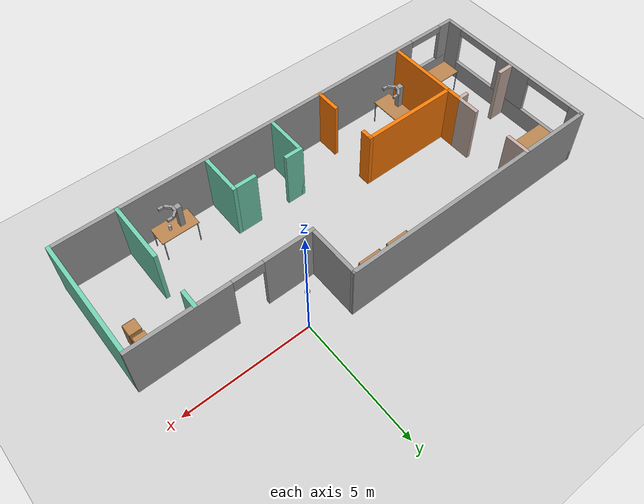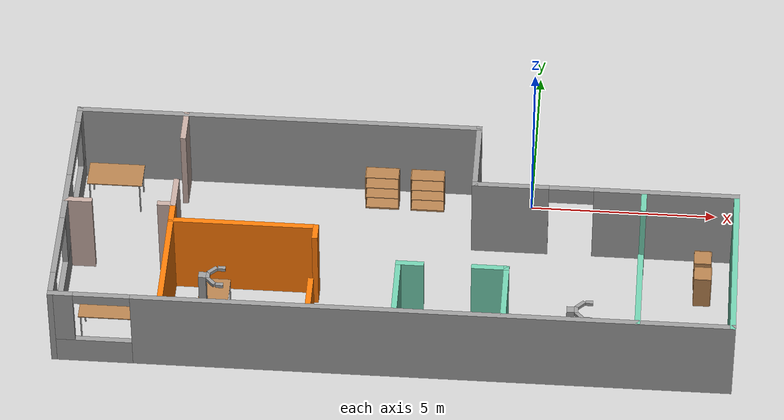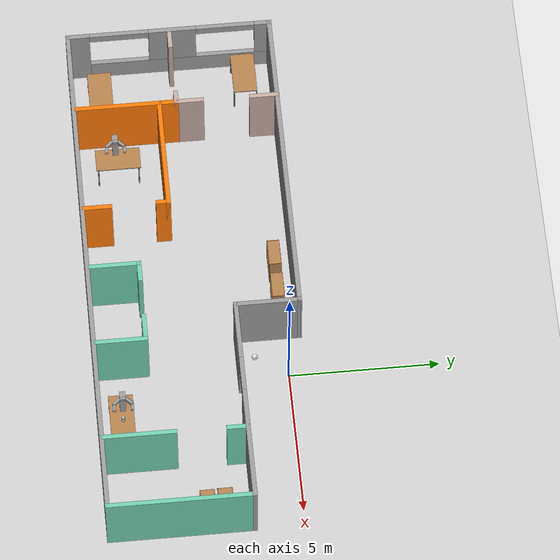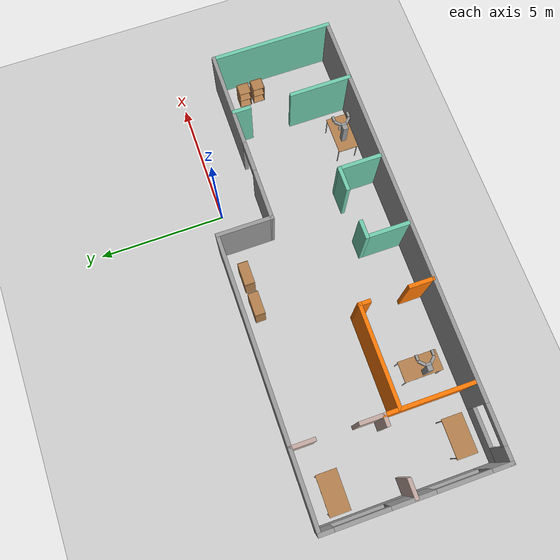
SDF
<sdf version="1.6">
 <world name="default">
  <plugin name="hello" filename="libhello.so"/>
  <light name="sun" type="directional">
   <pose>0 0 10 0 -0 0</pose>
   <diffuse>0.8 0.8 0.8 1</diffuse>
   <specular>0.2 0.2 0.2 1</specular>
   <attenuation>
    <range>1000</range>
    <constant>0.9</constant>
    <linear>0.01</linear>
    <quadratic>0.001</quadratic>
   </attenuation>
   <direction>-0.5 0.1 -0.9</direction>
  </light>
  <model name="ground_plane">
   <static>1</static>
   <link name="link">
    <collision name="collision">
     <geometry><plane><normal>0 0 1</normal><size>100 100</size></plane></geometry>
     <surface>
      <contact><collide_bitmask>65535</collide_bitmask></contact>
      <friction><ode><mu>100</mu><mu2>50</mu2></ode></friction>
     </surface>
    </collision>
    <visual name="visual">
     <cast_shadows>0</cast_shadows>
     <geometry><plane><normal>0 0 1</normal><size>100 100</size></plane></geometry>
     <material>
      <script><uri>file://media/materials/scripts/gazebo.material</uri><name>Gazebo/Grey</name></script>
     </material>
    </visual>
   </link>
  </model>
  <gravity>0 0 -9.8</gravity>
  <magnetic_field>6e-06 2.3e-05 -4.2e-05</magnetic_field>
  <atmosphere type="adiabatic"/>
  <physics name="default_physics" default="0" type="ode">
   <max_step_size>0.001</max_step_size>
   <real_time_factor>1</real_time_factor>
   <real_time_update_rate>1000</real_time_update_rate>
  </physics>
  <scene><ambient>0.4 0.4 0.4 1</ambient><background>0.7 0.7 0.7 1</background><shadows>1</shadows></scene>
  <spherical_coordinates>
   <surface_model>EARTH_WGS84</surface_model>
   <latitude_deg>0</latitude_deg>
   <longitude_deg>0</longitude_deg>
   <elevation>0</elevation>
   <heading_deg>0</heading_deg>
  </spherical_coordinates>
  <model name="Building">
   <pose>-3.41597 -2.95014 0 0 -0 0</pose>
   <link name="Wall_12">
    <collision name="Wall_12_Collision">
     <geometry><box><size>3.5 0.15 2.5</size></box></geometry>
     <pose>0 0 1.25 0 -0 0</pose>
    </collision>
    <visual name="Wall_12_Visual">
     <pose>0 0 1.25 0 -0 0</pose>
     <geometry><box><size>3.5 0.15 2.5</size></box></geometry>
     <material>
      <script><uri>file://media/materials/scripts/gazebo.material</uri><name>Gazebo/Grey</name></script>
      <ambient>0.996078 0.47451 0.0196078 1</ambient>
     </material>
     <meta><layer>0</layer></meta>
    </visual>
    <pose>-6.04441 -1.64552 0 0 0 -1.5708</pose>
   </link>
   <link name="Wall_16">
    <collision name="Wall_16_Collision">
     <geometry><box><size>11 0.15 2.5</size></box></geometry>
     <pose>0 0 1.25 0 -0 0</pose>
    </collision>
    <visual name="Wall_16_Visual">
     <pose>0 0 1.25 0 -0 0</pose>
     <geometry><box><size>11 0.15 2.5</size></box></geometry>
     <material>
      <script><uri>file://media/materials/scripts/gazebo.material</uri><name>Gazebo/Grey</name></script>
      <ambient>0.462745 0.490196 0.45098 1</ambient>
     </material>
     <meta><layer>0</layer></meta>
    </visual>
    <pose>-3.5 3.425 0 0 -0 0</pose>
   </link>
   <link name="Wall_17">
    <collision name="Wall_17_Collision">
     <geometry><box><size>2.25 0.15 2.5</size></box></geometry>
     <pose>0 0 1.25 0 -0 0</pose>
    </collision>
    <visual name="Wall_17_Visual">
     <pose>0 0 1.25 0 -0 0</pose>
     <geometry><box><size>2.25 0.15 2.5</size></box></geometry>
     <material>
      <script><uri>file://media/materials/scripts/gazebo.material</uri><name>Gazebo/Grey</name></script>
      <ambient>0.462745 0.490196 0.45098 1</ambient>
     </material>
     <meta><layer>0</layer></meta>
    </visual>
    <pose>1.92477 2.37476 0 0 0 -1.57101</pose>
   </link>
   <link name="Wall_18">
    <pose>5.42455 1.32452 0 0 -0 0</pose>
    <visual name="Wall_18_Visual_0">
     <pose>-2.54562 0 1.25 0 -0 0</pose>
     <geometry><box><size>2.05876 0.15 2.5</size></box></geometry>
     <material>
      <script><uri>file://media/materials/scripts/gazebo.material</uri><name>Gazebo/Grey</name></script>
      <ambient>0.462745 0.490196 0.45098 1</ambient>
     </material>
     <meta><layer>0</layer></meta>
    </visual>
    <collision name="Wall_18_Collision_0">
     <geometry><box><size>2.05876 0.15 2.5</size></box></geometry>
     <pose>-2.54562 0 1.25 0 -0 0</pose>
    </collision>
    <visual name="Wall_18_Visual_1">
     <pose>1.62938 0 1.25 0 -0 0</pose>
     <geometry><box><size>3.89124 0.15 2.5</size></box></geometry>
     <material>
      <script><uri>file://media/materials/scripts/gazebo.material</uri><name>Gazebo/Grey</name></script>
      <ambient>0.462745 0.490196 0.45098 1</ambient>
     </material>
     <meta><layer>0</layer></meta>
    </visual>
    <collision name="Wall_18_Collision_1">
     <geometry><box><size>3.89124 0.15 2.5</size></box></geometry>
     <pose>1.62938 0 1.25 0 -0 0</pose>
    </collision>
    <visual name="Wall_18_Visual_2">
     <pose>-0.916243 0 2.25 0 -0 0</pose>
     <geometry><box><size>1.2 0.15 0.5</size></box></geometry>
     <material>
      <script><uri>file://media/materials/scripts/gazebo.material</uri><name>Gazebo/Grey</name></script>
      <ambient>0.462745 0.490196 0.45098 1</ambient>
     </material>
     <meta><layer>0</layer></meta>
    </visual>
    <collision name="Wall_18_Collision_2">
     <geometry><box><size>1.2 0.15 0.5</size></box></geometry>
     <pose>-0.916243 0 2.25 0 -0 0</pose>
    </collision>
   </link>
   <link name="Wall_20">
    <collision name="Wall_20_Collision">
     <geometry><box><size>4 0.15 2.5</size></box></geometry>
     <pose>0 0 1.25 0 -0 0</pose>
    </collision>
    <visual name="Wall_20_Visual">
     <pose>0 0 1.25 0 -0 0</pose>
     <geometry><box><size>4 0.15 2.5</size></box></geometry>
     <material>
      <script><uri>file://media/materials/scripts/gazebo.material</uri><name>Gazebo/Grey</name></script>
      <ambient>0.996078 0.47451 0.0196078 1</ambient>
     </material>
     <meta><layer>0</layer></meta>
    </visual>
    <pose>-4.10848 -0.552329 0 0 -0 0</pose>
   </link>
   <link name="Wall_23">
    <collision name="Wall_23_Collision">
     <geometry><box><size>1.75 0.15 2.5</size></box></geometry>
     <pose>0 0 1.25 0 -0 0</pose>
    </collision>
    <visual name="Wall_23_Visual">
     <pose>0 0 1.25 0 -0 0</pose>
     <geometry><box><size>1.75 0.15 2.5</size></box></geometry>
     <material>
      <script><uri>file://media/materials/scripts/gazebo.material</uri><name>Gazebo/Grey</name></script>
      <ambient>0.435294 0.796078 0.67451 1</ambient>
     </material>
     <meta><layer>0</layer></meta>
    </visual>
    <pose>0.087622 -2.51323 0 0 0 -1.5708</pose>
   </link>
   <link name="Wall_32">
    <collision name="Wall_32_Collision">
     <geometry><box><size>2.5 0.15 2.5</size></box></geometry>
     <pose>0 0 1.25 0 -0 0</pose>
    </collision>
    <visual name="Wall_32_Visual">
     <pose>0 0 1.25 0 -0 0</pose>
     <geometry><box><size>2.5 0.15 2.5</size></box></geometry>
     <material>
      <script><uri>file://media/materials/scripts/gazebo.material</uri><name>Gazebo/Grey</name></script>
      <ambient>0.435294 0.796078 0.67451 1</ambient>
     </material>
     <meta><layer>0</layer></meta>
    </visual>
    <pose>6.4415 -2.22703 0 0 -0 1.5708</pose>
   </link>
   <link name="Wall_34">
    <collision name="Wall_34_Collision">
     <geometry><box><size>1.75 0.15 2.5</size></box></geometry>
     <pose>0 0 1.25 0 -0 0</pose>
    </collision>
    <visual name="Wall_34_Visual">
     <pose>0 0 1.25 0 -0 0</pose>
     <geometry><box><size>1.75 0.15 2.5</size></box></geometry>
     <material>
      <script><uri>file://media/materials/scripts/gazebo.material</uri><name>Gazebo/Grey</name></script>
      <ambient>0.435294 0.796078 0.67451 1</ambient>
     </material>
     <meta><layer>0</layer></meta>
    </visual>
    <pose>2.93762 -2.51323 0 0 0 -1.5708</pose>
   </link>
   <link name="Wall_36">
    <collision name="Wall_36_Collision">
     <geometry><box><size>0.75 0.15 2.5</size></box></geometry>
     <pose>0 0 1.25 0 -0 0</pose>
    </collision>
    <visual name="Wall_36_Visual">
     <pose>0 0 1.25 0 -0 0</pose>
     <geometry><box><size>0.75 0.15 2.5</size></box></geometry>
     <material>
      <script><uri>file://media/materials/scripts/gazebo.material</uri><name>Gazebo/Grey</name></script>
      <ambient>0.435294 0.796078 0.67451 1</ambient>
     </material>
     <meta><layer>0</layer></meta>
    </visual>
    <pose>6.45579 0.997622 0 0 -0 1.5708</pose>
   </link>
   <link name="Wall_38">
    <collision name="Wall_38_Collision">
     <geometry><box><size>0.75 0.15 2.5</size></box></geometry>
     <pose>0 0 1.25 0 -0 0</pose>
    </collision>
    <visual name="Wall_38_Visual">
     <pose>0 0 1.25 0 -0 0</pose>
     <geometry><box><size>0.75 0.15 2.5</size></box></geometry>
     <material>
      <script><uri>file://media/materials/scripts/gazebo.material</uri><name>Gazebo/Grey</name></script>
      <ambient>0.435294 0.796078 0.67451 1</ambient>
     </material>
     <meta><layer>0</layer></meta>
    </visual>
    <pose>0.387622 -1.71323 0 0 -0 0</pose>
   </link>
   <link name="Wall_40">
    <collision name="Wall_40_Collision">
     <geometry><box><size>1 0.15 2.5</size></box></geometry>
     <pose>0 0 1.25 0 -0 0</pose>
    </collision>
    <visual name="Wall_40_Visual">
     <pose>0 0 1.25 0 -0 0</pose>
     <geometry><box><size>1 0.15 2.5</size></box></geometry>
     <material>
      <script><uri>file://media/materials/scripts/gazebo.material</uri><name>Gazebo/Grey</name></script>
      <ambient>0.435294 0.796078 0.67451 1</ambient>
     </material>
     <meta><layer>0</layer></meta>
    </visual>
    <pose>2.51262 -1.71323 0 0 -0 3.14159</pose>
   </link>
   <link name="Wall_43">
    <collision name="Wall_43_Collision">
     <geometry><box><size>0.5 0.15 2.5</size></box></geometry>
     <pose>0 0 1.25 0 -0 0</pose>
    </collision>
    <visual name="Wall_43_Visual">
     <pose>0 0 1.25 0 -0 0</pose>
     <geometry><box><size>0.5 0.15 2.5</size></box></geometry>
     <material>
      <script><uri>file://media/materials/scripts/gazebo.material</uri><name>Gazebo/Grey</name></script>
      <ambient>0.996078 0.47451 0.0196078 1</ambient>
     </material>
     <meta><layer>0</layer></meta>
    </visual>
    <pose>-2.18348 -0.727329 0 0 0 -1.5708</pose>
   </link>
   <link name="Wall_45">
    <collision name="Wall_45_Collision">
     <geometry><box><size>1 0.15 2.5</size></box></geometry>
     <pose>0 0 1.25 0 -0 0</pose>
    </collision>
    <visual name="Wall_45_Visual">
     <pose>0 0 1.25 0 -0 0</pose>
     <geometry><box><size>1 0.15 2.5</size></box></geometry>
     <material>
      <script><uri>file://media/materials/scripts/gazebo.material</uri><name>Gazebo/Grey</name></script>
      <ambient>0.996078 0.47451 0.0196078 1</ambient>
     </material>
     <meta><layer>0</layer></meta>
    </visual>
    <pose>-2.16345 -2.92927 0 0 0 -1.5708</pose>
   </link>
   <link name="Wall_47">
    <collision name="Wall_47_Collision">
     <geometry><box><size>0.5 0.15 2.5</size></box></geometry>
     <pose>0 0 1.25 0 -0 0</pose>
    </collision>
    <visual name="Wall_47_Visual">
     <pose>0 0 1.25 0 -0 0</pose>
     <geometry><box><size>0.5 0.15 2.5</size></box></geometry>
     <material>
      <script><uri>file://media/materials/scripts/gazebo.material</uri><name>Gazebo/Grey</name></script>
      <ambient>0.760784 0.662745 0.627451 1</ambient>
     </material>
     <meta><layer>0</layer></meta>
    </visual>
    <pose>-6.21941 0.029484 0 0 -0 3.14159</pose>
   </link>
   <link name="Wall_49">
    <collision name="Wall_49_Collision">
     <geometry><box><size>0.75 0.15 2.5</size></box></geometry>
     <pose>0 0 1.25 0 -0 0</pose>
    </collision>
    <visual name="Wall_49_Visual">
     <pose>0 0 1.25 0 -0 0</pose>
     <geometry><box><size>0.75 0.15 2.5</size></box></geometry>
     <material>
      <script><uri>file://media/materials/scripts/gazebo.material</uri><name>Gazebo/Grey</name></script>
      <ambient>0.760784 0.662745 0.627451 1</ambient>
     </material>
     <meta><layer>0</layer></meta>
    </visual>
    <pose>-8.58628 0.017111 0 0 -0 3.14159</pose>
   </link>
   <link name="Wall_51">
    <collision name="Wall_51_Collision">
     <geometry><box><size>1 0.15 2.5</size></box></geometry>
     <pose>0 0 1.25 0 -0 0</pose>
    </collision>
    <visual name="Wall_51_Visual">
     <pose>0 0 1.25 0 -0 0</pose>
     <geometry><box><size>1 0.15 2.5</size></box></geometry>
     <material>
      <script><uri>file://media/materials/scripts/gazebo.material</uri><name>Gazebo/Grey</name></script>
      <ambient>0.760784 0.662745 0.627451 1</ambient>
     </material>
     <meta><layer>0</layer></meta>
    </visual>
    <pose>-6.04441 0.454485 0 0 -0 1.5708</pose>
   </link>
   <link name="Wall_55">
    <collision name="Wall_55_Collision">
     <geometry><box><size>1 0.15 2.5</size></box></geometry>
     <pose>0 0 1.25 0 -0 0</pose>
    </collision>
    <visual name="Wall_55_Visual">
     <pose>0 0 1.25 0 -0 0</pose>
     <geometry><box><size>1 0.15 2.5</size></box></geometry>
     <material>
      <script><uri>file://media/materials/scripts/gazebo.material</uri><name>Gazebo/Grey</name></script>
      <ambient>0.760784 0.662745 0.627451 1</ambient>
     </material>
     <meta><layer>0</layer></meta>
    </visual>
    <pose>-6.02797 2.98846 0 0 0 -1.5708</pose>
   </link>
   <link name="Wall_6">
    <collision name="Wall_6_Collision">
     <geometry><box><size>4.75 0.15 2.5</size></box></geometry>
     <pose>0 0 1.25 0 -0 0</pose>
    </collision>
    <visual name="Wall_6_Visual">
     <pose>0 0 1.25 0 -0 0</pose>
     <geometry><box><size>4.75 0.15 2.5</size></box></geometry>
     <material>
      <script><uri>file://media/materials/scripts/gazebo.material</uri><name>Gazebo/Grey</name></script>
      <ambient>0.435294 0.796078 0.67451 1</ambient>
     </material>
     <meta><layer>0</layer></meta>
    </visual>
    <pose>8.925 -1.125 0 0 0 -1.5708</pose>
   </link>
   <link name="Wall_8">
    <pose>0 -3.425 0 0 -0 3.14159</pose>
    <visual name="Wall_8_Visual_0">
     <pose>-1.08419 0 1.25 0 -0 0</pose>
     <geometry><box><size>15.8316 0.15 2.5</size></box></geometry>
     <material>
      <script><uri>file://media/materials/scripts/gazebo.material</uri><name>Gazebo/Grey</name></script>
      <ambient>0.462745 0.490196 0.45098 1</ambient>
     </material>
     <meta><layer>0</layer></meta>
    </visual>
    <collision name="Wall_8_Collision_0">
     <geometry><box><size>15.8316 0.15 2.5</size></box></geometry>
     <pose>-1.08419 0 1.25 0 -0 0</pose>
    </collision>
    <visual name="Wall_8_Visual_1">
     <pose>7.91581 0 0.4 0 -0 0</pose>
     <geometry><box><size>2.16839 0.15 0.8</size></box></geometry>
     <material>
      <script><uri>file://media/materials/scripts/gazebo.material</uri><name>Gazebo/Grey</name></script>
      <ambient>0.462745 0.490196 0.45098 1</ambient>
     </material>
     <meta><layer>0</layer></meta>
    </visual>
    <collision name="Wall_8_Collision_1">
     <geometry><box><size>2.16839 0.15 0.8</size></box></geometry>
     <pose>7.91581 0 0.4 0 -0 0</pose>
    </collision>
    <visual name="Wall_8_Visual_2">
     <pose>8.66581 0 1.65 0 -0 0</pose>
     <geometry><box><size>0.668389 0.15 1.7</size></box></geometry>
     <material>
      <script><uri>file://media/materials/scripts/gazebo.material</uri><name>Gazebo/Grey</name></script>
      <ambient>0.462745 0.490196 0.45098 1</ambient>
     </material>
     <meta><layer>0</layer></meta>
    </visual>
    <collision name="Wall_8_Collision_2">
     <geometry><box><size>0.668389 0.15 1.7</size></box></geometry>
     <pose>8.66581 0 1.65 0 -0 0</pose>
    </collision>
    <visual name="Wall_8_Visual_3">
     <pose>7.58161 0 2.35 0 -0 0</pose>
     <geometry><box><size>1.5 0.15 0.3</size></box></geometry>
     <material>
      <script><uri>file://media/materials/scripts/gazebo.material</uri><name>Gazebo/Grey</name></script>
      <ambient>0.462745 0.490196 0.45098 1</ambient>
     </material>
     <meta><layer>0</layer></meta>
    </visual>
    <collision name="Wall_8_Collision_3">
     <geometry><box><size>1.5 0.15 0.3</size></box></geometry>
     <pose>7.58161 0 2.35 0 -0 0</pose>
    </collision>
   </link>
   <link name="Wall_9">
    <pose>-8.925 0 0 0 -0 1.5708</pose>
    <visual name="Wall_9_Visual_0">
     <pose>-3.09367 0 1.25 0 -0 0</pose>
     <geometry><box><size>0.812669 0.15 2.5</size></box></geometry>
     <material>
      <script><uri>file://media/materials/scripts/gazebo.material</uri><name>Gazebo/Grey</name></script>
      <ambient>0.462745 0.490196 0.45098 1</ambient>
     </material>
     <meta><layer>0</layer></meta>
    </visual>
    <collision name="Wall_9_Collision_0">
     <geometry><box><size>0.812669 0.15 2.5</size></box></geometry>
     <pose>-3.09367 0 1.25 0 -0 0</pose>
    </collision>
    <visual name="Wall_9_Visual_1">
     <pose>0.406335 0 0.4 0 -0 0</pose>
     <geometry><box><size>6.18733 0.15 0.8</size></box></geometry>
     <material>
      <script><uri>file://media/materials/scripts/gazebo.material</uri><name>Gazebo/Grey</name></script>
      <ambient>0.462745 0.490196 0.45098 1</ambient>
     </material>
     <meta><layer>0</layer></meta>
    </visual>
    <collision name="Wall_9_Collision_1">
     <geometry><box><size>6.18733 0.15 0.8</size></box></geometry>
     <pose>0.406335 0 0.4 0 -0 0</pose>
    </collision>
    <visual name="Wall_9_Visual_2">
     <pose>0.115345 0 1.65 0 -0 0</pose>
     <geometry><box><size>1.60535 0.15 1.7</size></box></geometry>
     <material>
      <script><uri>file://media/materials/scripts/gazebo.material</uri><name>Gazebo/Grey</name></script>
      <ambient>0.462745 0.490196 0.45098 1</ambient>
     </material>
     <meta><layer>0</layer></meta>
    </visual>
    <collision name="Wall_9_Collision_2">
     <geometry><box><size>1.60535 0.15 1.7</size></box></geometry>
     <pose>0.115345 0 1.65 0 -0 0</pose>
    </collision>
    <visual name="Wall_9_Visual_3">
     <pose>3.20901 0 1.65 0 -0 0</pose>
     <geometry><box><size>0.581978 0.15 1.7</size></box></geometry>
     <material>
      <script><uri>file://media/materials/scripts/gazebo.material</uri><name>Gazebo/Grey</name></script>
      <ambient>0.462745 0.490196 0.45098 1</ambient>
     </material>
     <meta><layer>0</layer></meta>
    </visual>
    <collision name="Wall_9_Collision_3">
     <geometry><box><size>0.581978 0.15 1.7</size></box></geometry>
     <pose>3.20901 0 1.65 0 -0 0</pose>
    </collision>
    <visual name="Wall_9_Visual_4">
     <pose>-1.68733 0 2.35 0 -0 0</pose>
     <geometry><box><size>2 0.15 0.3</size></box></geometry>
     <material>
      <script><uri>file://media/materials/scripts/gazebo.material</uri><name>Gazebo/Grey</name></script>
      <ambient>0.462745 0.490196 0.45098 1</ambient>
     </material>
     <meta><layer>0</layer></meta>
    </visual>
    <collision name="Wall_9_Collision_4">
     <geometry><box><size>2 0.15 0.3</size></box></geometry>
     <pose>-1.68733 0 2.35 0 -0 0</pose>
    </collision>
    <visual name="Wall_9_Visual_5">
     <pose>1.91802 0 2.35 0 -0 0</pose>
     <geometry><box><size>2 0.15 0.3</size></box></geometry>
     <material>
      <script><uri>file://media/materials/scripts/gazebo.material</uri><name>Gazebo/Grey</name></script>
      <ambient>0.462745 0.490196 0.45098 1</ambient>
     </material>
     <meta><layer>0</layer></meta>
    </visual>
    <collision name="Wall_9_Collision_5">
     <geometry><box><size>2 0.15 0.3</size></box></geometry>
     <pose>1.91802 0 2.35 0 -0 0</pose>
    </collision>
   </link>
   <static>1</static>
  </model>
  <model name="table">
   <static>1</static>
   <link name="link">
    <collision name="surface">
     <pose>0 0 1 0 -0 0</pose>
     <geometry><box><size>1.5 0.8 0.03</size></box></geometry>
     <surface><friction><ode><mu>0.6</mu><mu2>0.6</mu2></ode></friction></surface>
    </collision>
    <visual name="visual1">
     <pose>0 0 1 0 -0 0</pose>
     <geometry><box><size>1.5 0.8 0.03</size></box></geometry>
     <material>
      <script><uri>file://media/materials/scripts/gazebo.material</uri><name>Gazebo/Wood</name></script>
     </material>
    </visual>
    <collision name="front_left_leg">
     <pose>0.68 0.38 0.5 0 -0 0</pose>
     <geometry><cylinder><radius>0.02</radius><length>1</length></cylinder></geometry>
    </collision>
    <visual name="front_left_leg">
     <pose>0.68 0.38 0.5 0 -0 0</pose>
     <geometry><cylinder><radius>0.02</radius><length>1</length></cylinder></geometry>
     <material>
      <script><uri>file://media/materials/scripts/gazebo.material</uri><name>Gazebo/Grey</name></script>
     </material>
    </visual>
    <collision name="front_right_leg">
     <pose>0.68 -0.38 0.5 0 -0 0</pose>
     <geometry><cylinder><radius>0.02</radius><length>1</length></cylinder></geometry>
    </collision>
    <visual name="front_right_leg">
     <pose>0.68 -0.38 0.5 0 -0 0</pose>
     <geometry><cylinder><radius>0.02</radius><length>1</length></cylinder></geometry>
     <material>
      <script><uri>file://media/materials/scripts/gazebo.material</uri><name>Gazebo/Grey</name></script>
     </material>
    </visual>
    <collision name="back_right_leg">
     <pose>-0.68 -0.38 0.5 0 -0 0</pose>
     <geometry><cylinder><radius>0.02</radius><length>1</length></cylinder></geometry>
    </collision>
    <visual name="back_right_leg">
     <pose>-0.68 -0.38 0.5 0 -0 0</pose>
     <geometry><cylinder><radius>0.02</radius><length>1</length></cylinder></geometry>
     <material>
      <script><uri>file://media/materials/scripts/gazebo.material</uri><name>Gazebo/Grey</name></script>
     </material>
    </visual>
    <collision name="back_left_leg">
     <pose>-0.68 0.38 0.5 0 -0 0</pose>
     <geometry><cylinder><radius>0.02</radius><length>1</length></cylinder></geometry>
    </collision>
    <visual name="back_left_leg">
     <pose>-0.68 0.38 0.5 0 -0 0</pose>
     <geometry><cylinder><radius>0.02</radius><length>1</length></cylinder></geometry>
     <material>
      <script><uri>file://media/materials/scripts/gazebo.material</uri><name>Gazebo/Grey</name></script>
     </material>
    </visual>
   </link>
   <pose>-11.3202 -0.485992 0 0 -0 0</pose>
  </model>
  <model name="table_0">
   <static>1</static>
   <link name="link">
    <collision name="surface">
     <pose>0 0 1 0 -0 0</pose>
     <geometry><box><size>1.5 0.8 0.03</size></box></geometry>
     <surface><friction><ode><mu>0.6</mu><mu2>0.6</mu2></ode></friction></surface>
    </collision>
    <visual name="visual1">
     <pose>0 0 1 0 -0 0</pose>
     <geometry><box><size>1.5 0.8 0.03</size></box></geometry>
     <material>
      <script><uri>file://media/materials/scripts/gazebo.material</uri><name>Gazebo/Wood</name></script>
     </material>
    </visual>
    <collision name="front_left_leg">
     <pose>0.68 0.38 0.5 0 -0 0</pose>
     <geometry><cylinder><radius>0.02</radius><length>1</length></cylinder></geometry>
    </collision>
    <visual name="front_left_leg">
     <pose>0.68 0.38 0.5 0 -0 0</pose>
     <geometry><cylinder><radius>0.02</radius><length>1</length></cylinder></geometry>
     <material>
      <script><uri>file://media/materials/scripts/gazebo.material</uri><name>Gazebo/Grey</name></script>
     </material>
    </visual>
    <collision name="front_right_leg">
     <pose>0.68 -0.38 0.5 0 -0 0</pose>
     <geometry><cylinder><radius>0.02</radius><length>1</length></cylinder></geometry>
    </collision>
    <visual name="front_right_leg">
     <pose>0.68 -0.38 0.5 0 -0 0</pose>
     <geometry><cylinder><radius>0.02</radius><length>1</length></cylinder></geometry>
     <material>
      <script><uri>file://media/materials/scripts/gazebo.material</uri><name>Gazebo/Grey</name></script>
     </material>
    </visual>
    <collision name="back_right_leg">
     <pose>-0.68 -0.38 0.5 0 -0 0</pose>
     <geometry><cylinder><radius>0.02</radius><length>1</length></cylinder></geometry>
    </collision>
    <visual name="back_right_leg">
     <pose>-0.68 -0.38 0.5 0 -0 0</pose>
     <geometry><cylinder><radius>0.02</radius><length>1</length></cylinder></geometry>
     <material>
      <script><uri>file://media/materials/scripts/gazebo.material</uri><name>Gazebo/Grey</name></script>
     </material>
    </visual>
    <collision name="back_left_leg">
     <pose>-0.68 0.38 0.5 0 -0 0</pose>
     <geometry><cylinder><radius>0.02</radius><length>1</length></cylinder></geometry>
    </collision>
    <visual name="back_left_leg">
     <pose>-0.68 0.38 0.5 0 -0 0</pose>
     <geometry><cylinder><radius>0.02</radius><length>1</length></cylinder></geometry>
     <material>
      <script><uri>file://media/materials/scripts/gazebo.material</uri><name>Gazebo/Grey</name></script>
     </material>
    </visual>
   </link>
   <pose>-8.22656 -5.02138 0.088089 0 -0 1.5707</pose>
  </model>
  <model name="cabinet">
   <static>1</static>
   <link name="cabinet_bottom_plate">
    <inertial>
     <pose>0 0 -1 0 -0 0</pose>
     <inertia><ixx>2.05</ixx><ixy>0</ixy><ixz>0</ixz><iyy>2.05</iyy><iyz>0</iyz><izz>2.05</izz></inertia>
     <mass>25</mass>
    </inertial>
    <collision name="cabinet_bottom_plate_geom">
     <pose>0 0 0.01 0 -0 0</pose>
     <geometry><box><size>0.45 0.45 0.02</size></box></geometry>
    </collision>
    <visual name="cabinet_bottom_plate_geom_visual">
     <pose>0 0 0.01 0 -0 0</pose>
     <geometry><box><size>0.45 0.45 0.02</size></box></geometry>
     <material>
      <script><uri>file://media/materials/scripts/gazebo.material</uri><name>Gazebo/Wood</name></script>
     </material>
    </visual>
    <collision name="cabinet_bottom_plate_geom_cabinet_back_plate">
     <pose>0.235 0 0.51 0 -0 0</pose>
     <geometry><box><size>0.02 0.45 1.02</size></box></geometry>
    </collision>
    <visual name="cabinet_bottom_plate_geom_cabinet_back_plate_visual">
     <pose>0.235 0 0.51 0 -0 0</pose>
     <geometry><box><size>0.02 0.45 1.02</size></box></geometry>
     <material>
      <script><uri>file://media/materials/scripts/gazebo.material</uri><name>Gazebo/Wood</name></script>
     </material>
    </visual>
    <collision name="cabinet_bottom_plate_geom_cabinet_left_plate">
     <pose>0 0.235 0.51 0 -0 0</pose>
     <geometry><box><size>0.45 0.02 1.02</size></box></geometry>
    </collision>
    <visual name="cabinet_bottom_plate_geom_cabinet_left_plate_visual">
     <pose>0 0.235 0.51 0 -0 0</pose>
     <geometry><box><size>0.45 0.02 1.02</size></box></geometry>
     <material>
      <script><uri>file://media/materials/scripts/gazebo.material</uri><name>Gazebo/Wood</name></script>
     </material>
    </visual>
    <collision name="cabinet_bottom_plate_geom_cabinet_middle_plate">
     <pose>0 0 0.51 0 -0 0</pose>
     <geometry><box><size>0.45 0.45 0.02</size></box></geometry>
    </collision>
    <visual name="cabinet_bottom_plate_geom_cabinet_middle_plate_visual">
     <pose>0 0 0.51 0 -0 0</pose>
     <geometry><box><size>0.45 0.45 0.02</size></box></geometry>
     <material>
      <script><uri>file://media/materials/scripts/gazebo.material</uri><name>Gazebo/Wood</name></script>
     </material>
    </visual>
    <collision name="cabinet_bottom_plate_geom_cabinet_right_plate">
     <pose>0 -0.235 0.51 0 -0 0</pose>
     <geometry><box><size>0.45 0.02 1.02</size></box></geometry>
    </collision>
    <visual name="cabinet_bottom_plate_geom_cabinet_right_plate_visual">
     <pose>0 -0.235 0.51 0 -0 0</pose>
     <geometry><box><size>0.45 0.02 1.02</size></box></geometry>
     <material>
      <script><uri>file://media/materials/scripts/gazebo.material</uri><name>Gazebo/Wood</name></script>
     </material>
    </visual>
    <collision name="cabinet_bottom_plate_geom_cabinet_top_plate">
     <pose>0 0 1.01 0 -0 0</pose>
     <geometry><box><size>0.45 0.45 0.02</size></box></geometry>
    </collision>
    <visual name="cabinet_bottom_plate_geom_cabinet_top_plate_visual">
     <pose>0 0 1.01 0 -0 0</pose>
     <geometry><box><size>0.45 0.45 0.02</size></box></geometry>
     <material>
      <script><uri>file://media/materials/scripts/gazebo.material</uri><name>Gazebo/Wood</name></script>
     </material>
    </visual>
   </link>
   <pose>4.68279 -2.5185 0 0 -0 0</pose>
  </model>
  <model name="bookshelf">
   <static>1</static>
   <link name="link">
    <inertial><mass>1</mass></inertial>
    <collision name="back">
     <pose>0 0.005 0.6 0 -0 0</pose>
     <geometry><box><size>0.9 0.01 1.2</size></box></geometry>
    </collision>
    <visual name="visual1">
     <pose>0 0.005 0.6 0 -0 0</pose>
     <geometry><box><size>0.9 0.01 1.2</size></box></geometry>
     <material>
      <script><uri>file://media/materials/scripts/gazebo.material</uri><name>Gazebo/Wood</name></script>
     </material>
    </visual>
    <collision name="left_side">
     <pose>0.45 -0.195 0.6 0 -0 0</pose>
     <geometry><box><size>0.02 0.4 1.2</size></box></geometry>
    </collision>
    <visual name="visual2">
     <pose>0.45 -0.195 0.6 0 -0 0</pose>
     <geometry><box><size>0.02 0.4 1.2</size></box></geometry>
     <material>
      <script><uri>file://media/materials/scripts/gazebo.material</uri><name>Gazebo/Wood</name></script>
     </material>
    </visual>
    <collision name="right_side">
     <pose>-0.45 -0.195 0.6 0 -0 0</pose>
     <geometry><box><size>0.02 0.4 1.2</size></box></geometry>
    </collision>
    <visual name="visual3">
     <pose>-0.45 -0.195 0.6 0 -0 0</pose>
     <geometry><box><size>0.02 0.4 1.2</size></box></geometry>
     <material>
      <script><uri>file://media/materials/scripts/gazebo.material</uri><name>Gazebo/Wood</name></script>
     </material>
    </visual>
    <collision name="bottom">
     <pose>0 -0.195 0.03 0 -0 0</pose>
     <geometry><box><size>0.88 0.4 0.06</size></box></geometry>
    </collision>
    <visual name="visual4">
     <pose>0 -0.195 0.03 0 -0 0</pose>
     <geometry><box><size>0.88 0.4 0.06</size></box></geometry>
     <material>
      <script><uri>file://media/materials/scripts/gazebo.material</uri><name>Gazebo/Wood</name></script>
     </material>
    </visual>
    <collision name="top">
     <pose>0 -0.195 1.19 0 -0 0</pose>
     <geometry><box><size>0.88 0.4 0.02</size></box></geometry>
    </collision>
    <visual name="visual5">
     <pose>0 -0.195 1.19 0 -0 0</pose>
     <geometry><box><size>0.88 0.4 0.02</size></box></geometry>
     <material>
      <script><uri>file://media/materials/scripts/gazebo.material</uri><name>Gazebo/Wood</name></script>
     </material>
    </visual>
    <collision name="low_shelf">
     <pose>0 -0.195 0.43 0 -0 0</pose>
     <geometry><box><size>0.88 0.4 0.02</size></box></geometry>
    </collision>
    <visual name="visual6">
     <pose>0 -0.195 0.43 0 -0 0</pose>
     <geometry><box><size>0.88 0.4 0.02</size></box></geometry>
     <material>
      <script><uri>file://media/materials/scripts/gazebo.material</uri><name>Gazebo/Wood</name></script>
     </material>
    </visual>
    <collision name="high_shelf">
     <pose>0 -0.195 0.8 0 -0 0</pose>
     <geometry><box><size>0.88 0.4 0.02</size></box></geometry>
    </collision>
    <visual name="visual7">
     <pose>0 -0.195 0.8 0 -0 0</pose>
     <geometry><box><size>0.88 0.4 0.02</size></box></geometry>
     <material>
      <script><uri>file://media/materials/scripts/gazebo.material</uri><name>Gazebo/Wood</name></script>
     </material>
    </visual>
   </link>
   <pose>-2.84106 0.072068 0 0 -0 0</pose>
  </model>
  <model name="cabinet_0">
   <static>1</static>
   <link name="cabinet_bottom_plate">
    <inertial>
     <pose>0 0 -1 0 -0 0</pose>
     <inertia><ixx>2.05</ixx><ixy>0</ixy><ixz>0</ixz><iyy>2.05</iyy><iyz>0</iyz><izz>2.05</izz></inertia>
     <mass>25</mass>
    </inertial>
    <collision name="cabinet_bottom_plate_geom">
     <pose>0 0 0.01 0 -0 0</pose>
     <geometry><box><size>0.45 0.45 0.02</size></box></geometry>
    </collision>
    <visual name="cabinet_bottom_plate_geom_visual">
     <pose>0 0 0.01 0 -0 0</pose>
     <geometry><box><size>0.45 0.45 0.02</size></box></geometry>
     <material>
      <script><uri>file://media/materials/scripts/gazebo.material</uri><name>Gazebo/Wood</name></script>
     </material>
    </visual>
    <collision name="cabinet_bottom_plate_geom_cabinet_back_plate">
     <pose>0.235 0 0.51 0 -0 0</pose>
     <geometry><box><size>0.02 0.45 1.02</size></box></geometry>
    </collision>
    <visual name="cabinet_bottom_plate_geom_cabinet_back_plate_visual">
     <pose>0.235 0 0.51 0 -0 0</pose>
     <geometry><box><size>0.02 0.45 1.02</size></box></geometry>
     <material>
      <script><uri>file://media/materials/scripts/gazebo.material</uri><name>Gazebo/Wood</name></script>
     </material>
    </visual>
    <collision name="cabinet_bottom_plate_geom_cabinet_left_plate">
     <pose>0 0.235 0.51 0 -0 0</pose>
     <geometry><box><size>0.45 0.02 1.02</size></box></geometry>
    </collision>
    <visual name="cabinet_bottom_plate_geom_cabinet_left_plate_visual">
     <pose>0 0.235 0.51 0 -0 0</pose>
     <geometry><box><size>0.45 0.02 1.02</size></box></geometry>
     <material>
      <script><uri>file://media/materials/scripts/gazebo.material</uri><name>Gazebo/Wood</name></script>
     </material>
    </visual>
    <collision name="cabinet_bottom_plate_geom_cabinet_middle_plate">
     <pose>0 0 0.51 0 -0 0</pose>
     <geometry><box><size>0.45 0.45 0.02</size></box></geometry>
    </collision>
    <visual name="cabinet_bottom_plate_geom_cabinet_middle_plate_visual">
     <pose>0 0 0.51 0 -0 0</pose>
     <geometry><box><size>0.45 0.45 0.02</size></box></geometry>
     <material>
      <script><uri>file://media/materials/scripts/gazebo.material</uri><name>Gazebo/Wood</name></script>
     </material>
    </visual>
    <collision name="cabinet_bottom_plate_geom_cabinet_right_plate">
     <pose>0 -0.235 0.51 0 -0 0</pose>
     <geometry><box><size>0.45 0.02 1.02</size></box></geometry>
    </collision>
    <visual name="cabinet_bottom_plate_geom_cabinet_right_plate_visual">
     <pose>0 -0.235 0.51 0 -0 0</pose>
     <geometry><box><size>0.45 0.02 1.02</size></box></geometry>
     <material>
      <script><uri>file://media/materials/scripts/gazebo.material</uri><name>Gazebo/Wood</name></script>
     </material>
    </visual>
    <collision name="cabinet_bottom_plate_geom_cabinet_top_plate">
     <pose>0 0 1.01 0 -0 0</pose>
     <geometry><box><size>0.45 0.45 0.02</size></box></geometry>
    </collision>
    <visual name="cabinet_bottom_plate_geom_cabinet_top_plate_visual">
     <pose>0 0 1.01 0 -0 0</pose>
     <geometry><box><size>0.45 0.45 0.02</size></box></geometry>
     <material>
      <script><uri>file://media/materials/scripts/gazebo.material</uri><name>Gazebo/Wood</name></script>
     </material>
    </visual>
   </link>
   <pose>4.70024 -3.10262 0 0 -0 0</pose>
  </model>
  <model name="RobotGripper">
   <link name="link_0">
    <pose>-0.270333 0 -0.375 0 -0 0</pose>
    <inertial>
     <mass>1</mass>
     <inertia>
      <ixx>0.166667</ixx>
      <ixy>0</ixy>
      <ixz>0</ixz>
      <iyy>0.166667</iyy>
      <iyz>0</iyz>
      <izz>0.166667</izz>
     </inertia>
     <pose>0 0 -0.5 0 -0 0</pose>
    </inertial>
    <visual name="visual">
     <geometry><box><size>0.2 0.2 1</size></box></geometry>
     <material>
      <lighting>1</lighting>
      <script><uri>file://media/materials/scripts/gazebo.material</uri><name>Gazebo/Grey</name></script>
      <shader type="pixel"><normal_map>__default__</normal_map></shader>
      <ambient>0.3 0.3 0.3 1</ambient>
      <diffuse>0.7 0.7 0.7 1</diffuse>
      <specular>0.01 0.01 0.01 1</specular>
      <emissive>0 0 0 1</emissive>
     </material>
    </visual>
    <collision name="collision">
     <geometry><box><size>0.2 0.2 1</size></box></geometry>
     <surface>
      <friction>
       <ode><mu>1</mu><mu2>1</mu2><fdir1>0 0 0</fdir1><slip1>0</slip1><slip2>0</slip2></ode>
       <torsional>
        <coefficient>1</coefficient>
        <patch_radius>0</patch_radius>
        <surface_radius>0</surface_radius>
        <use_patch_radius>1</use_patch_radius>
        <ode><slip>0</slip></ode>
       </torsional>
      </friction>
      <bounce><restitution_coefficient>0</restitution_coefficient><threshold>1e+06</threshold></bounce>
      <contact>
       <collide_without_contact>0</collide_without_contact>
       <collide_without_contact_bitmask>1</collide_without_contact_bitmask>
       <collide_bitmask>1</collide_bitmask>
       <ode>
        <soft_cfm>0</soft_cfm>
        <soft_erp>0.2</soft_erp>
        <kp>1e+13</kp>
        <kd>1</kd>
        <max_vel>0.01</max_vel>
        <min_depth>0</min_depth>
       </ode>
       <bullet>
        <split_impulse>1</split_impulse>
        <split_impulse_penetration_threshold>-0.01</split_impulse_penetration_threshold>
        <soft_cfm>0</soft_cfm>
        <soft_erp>0.2</soft_erp>
        <kp>1e+13</kp>
        <kd>1</kd>
       </bullet>
      </contact>
     </surface>
    </collision>
   </link>
   <link name="link_1">
    <pose>-0.120333 0 0.075 0 -0 0</pose>
    <inertial>
     <mass>1</mass>
     <inertia>
      <ixx>0.166667</ixx>
      <ixy>0</ixy>
      <ixz>0</ixz>
      <iyy>0.166667</iyy>
      <iyz>0</iyz>
      <izz>0.166667</izz>
     </inertia>
    </inertial>
    <visual name="visual">
     <geometry><box><size>0.1 0.2 0.1</size></box></geometry>
     <material>
      <lighting>1</lighting>
      <script><uri>file://media/materials/scripts/gazebo.material</uri><name>Gazebo/Grey</name></script>
      <shader type="pixel"><normal_map>__default__</normal_map></shader>
      <ambient>0.3 0.3 0.3 1</ambient>
      <diffuse>0.7 0.7 0.7 1</diffuse>
      <specular>0.01 0.01 0.01 1</specular>
      <emissive>0 0 0 1</emissive>
     </material>
    </visual>
    <collision name="collision">
     <geometry><box><size>0.1 0.2 0.1</size></box></geometry>
     <surface>
      <friction>
       <ode><mu>1</mu><mu2>1</mu2><fdir1>0 0 0</fdir1><slip1>0</slip1><slip2>0</slip2></ode>
       <torsional>
        <coefficient>1</coefficient>
        <patch_radius>0</patch_radius>
        <surface_radius>0</surface_radius>
        <use_patch_radius>1</use_patch_radius>
        <ode><slip>0</slip></ode>
       </torsional>
      </friction>
      <bounce><restitution_coefficient>0</restitution_coefficient><threshold>1e+06</threshold></bounce>
      <contact>
       <collide_without_contact>0</collide_without_contact>
       <collide_without_contact_bitmask>1</collide_without_contact_bitmask>
       <collide_bitmask>1</collide_bitmask>
       <ode>
        <soft_cfm>0</soft_cfm>
        <soft_erp>0.2</soft_erp>
        <kp>1e+13</kp>
        <kd>1</kd>
        <max_vel>0.01</max_vel>
        <min_depth>0</min_depth>
       </ode>
       <bullet>
        <split_impulse>1</split_impulse>
        <split_impulse_penetration_threshold>-0.01</split_impulse_penetration_threshold>
        <soft_cfm>0</soft_cfm>
        <soft_erp>0.2</soft_erp>
        <kp>1e+13</kp>
        <kd>1</kd>
       </bullet>
      </contact>
     </surface>
    </collision>
   </link>
   <link name="link_2">
    <pose>-0.020333 0.2 0.075 0 0 -0.78539</pose>
    <inertial>
     <mass>1</mass>
     <inertia>
      <ixx>0.166667</ixx>
      <ixy>0</ixy>
      <ixz>0</ixz>
      <iyy>0.166667</iyy>
      <iyz>0</iyz>
      <izz>0.166667</izz>
     </inertia>
    </inertial>
    <visual name="visual">
     <geometry><box><size>0.1 0.3 0.1</size></box></geometry>
     <material>
      <lighting>1</lighting>
      <script><uri>file://media/materials/scripts/gazebo.material</uri><name>Gazebo/Grey</name></script>
      <shader type="pixel"><normal_map>__default__</normal_map></shader>
      <ambient>0.3 0.3 0.3 1</ambient>
      <diffuse>0.7 0.7 0.7 1</diffuse>
      <specular>0.01 0.01 0.01 1</specular>
      <emissive>0 0 0 1</emissive>
     </material>
    </visual>
    <collision name="collision">
     <geometry><box><size>0.1 0.3 0.1</size></box></geometry>
     <surface>
      <friction>
       <ode><mu>1</mu><mu2>1</mu2><fdir1>0 0 0</fdir1><slip1>0</slip1><slip2>0</slip2></ode>
       <torsional>
        <coefficient>1</coefficient>
        <patch_radius>0</patch_radius>
        <surface_radius>0</surface_radius>
        <use_patch_radius>1</use_patch_radius>
        <ode><slip>0</slip></ode>
       </torsional>
      </friction>
      <bounce><restitution_coefficient>0</restitution_coefficient><threshold>1e+06</threshold></bounce>
      <contact>
       <collide_without_contact>0</collide_without_contact>
       <collide_without_contact_bitmask>1</collide_without_contact_bitmask>
       <collide_bitmask>1</collide_bitmask>
       <ode>
        <soft_cfm>0</soft_cfm>
        <soft_erp>0.2</soft_erp>
        <kp>1e+13</kp>
        <kd>1</kd>
        <max_vel>0.01</max_vel>
        <min_depth>0</min_depth>
       </ode>
       <bullet>
        <split_impulse>1</split_impulse>
        <split_impulse_penetration_threshold>-0.01</split_impulse_penetration_threshold>
        <soft_cfm>0</soft_cfm>
        <soft_erp>0.2</soft_erp>
        <kp>1e+13</kp>
        <kd>1</kd>
       </bullet>
      </contact>
     </surface>
    </collision>
   </link>
   <link name="link_2_clone">
    <pose>-0.020333 -0.2 0.075 0 -0 0.78539</pose>
    <inertial>
     <mass>1</mass>
     <inertia>
      <ixx>0.166667</ixx>
      <ixy>0</ixy>
      <ixz>0</ixz>
      <iyy>0.166667</iyy>
      <iyz>0</iyz>
      <izz>0.166667</izz>
     </inertia>
    </inertial>
    <visual name="visual">
     <geometry><box><size>0.1 0.3 0.1</size></box></geometry>
     <material>
      <lighting>1</lighting>
      <script><uri>file://media/materials/scripts/gazebo.material</uri><name>Gazebo/Grey</name></script>
      <shader type="pixel"><normal_map>__default__</normal_map></shader>
      <ambient>0.3 0.3 0.3 1</ambient>
      <diffuse>0.7 0.7 0.7 1</diffuse>
      <specular>0.01 0.01 0.01 1</specular>
      <emissive>0 0 0 1</emissive>
     </material>
    </visual>
    <collision name="collision">
     <geometry><box><size>0.1 0.3 0.1</size></box></geometry>
     <surface>
      <friction>
       <ode><mu>1</mu><mu2>1</mu2><fdir1>0 0 0</fdir1><slip1>0</slip1><slip2>0</slip2></ode>
       <torsional>
        <coefficient>1</coefficient>
        <patch_radius>0</patch_radius>
        <surface_radius>0</surface_radius>
        <use_patch_radius>1</use_patch_radius>
        <ode><slip>0</slip></ode>
       </torsional>
      </friction>
      <bounce><restitution_coefficient>0</restitution_coefficient><threshold>1e+06</threshold></bounce>
      <contact>
       <collide_without_contact>0</collide_without_contact>
       <collide_without_contact_bitmask>1</collide_without_contact_bitmask>
       <collide_bitmask>1</collide_bitmask>
       <ode>
        <soft_cfm>0</soft_cfm>
        <soft_erp>0.2</soft_erp>
        <kp>1e+13</kp>
        <kd>1</kd>
        <max_vel>0.01</max_vel>
        <min_depth>0</min_depth>
       </ode>
       <bullet>
        <split_impulse>1</split_impulse>
        <split_impulse_penetration_threshold>-0.01</split_impulse_penetration_threshold>
        <soft_cfm>0</soft_cfm>
        <soft_erp>0.2</soft_erp>
        <kp>1e+13</kp>
        <kd>1</kd>
       </bullet>
      </contact>
     </surface>
    </collision>
   </link>
   <link name="link_3">
    <pose>0.215667 0.3 0.075 0 -0 1.5707</pose>
    <inertial>
     <mass>1</mass>
     <inertia>
      <ixx>0.166667</ixx>
      <ixy>0</ixy>
      <ixz>0</ixz>
      <iyy>0.166667</iyy>
      <iyz>0</iyz>
      <izz>0.166667</izz>
     </inertia>
    </inertial>
    <visual name="visual">
     <geometry><box><size>0.1 0.2 0.1</size></box></geometry>
     <material>
      <lighting>1</lighting>
      <script><uri>file://media/materials/scripts/gazebo.material</uri><name>Gazebo/Grey</name></script>
      <shader type="pixel"><normal_map>__default__</normal_map></shader>
      <ambient>0.3 0.3 0.3 1</ambient>
      <diffuse>0.7 0.7 0.7 1</diffuse>
      <specular>0.01 0.01 0.01 1</specular>
      <emissive>0 0 0 1</emissive>
     </material>
    </visual>
    <collision name="collision">
     <geometry><box><size>0.1 0.2 0.1</size></box></geometry>
     <surface>
      <friction>
       <ode><mu>1</mu><mu2>1</mu2><fdir1>0 0 0</fdir1><slip1>0</slip1><slip2>0</slip2></ode>
       <torsional>
        <coefficient>1</coefficient>
        <patch_radius>0</patch_radius>
        <surface_radius>0</surface_radius>
        <use_patch_radius>1</use_patch_radius>
        <ode><slip>0</slip></ode>
       </torsional>
      </friction>
      <bounce><restitution_coefficient>0</restitution_coefficient><threshold>1e+06</threshold></bounce>
      <contact>
       <collide_without_contact>0</collide_without_contact>
       <collide_without_contact_bitmask>1</collide_without_contact_bitmask>
       <collide_bitmask>1</collide_bitmask>
       <ode>
        <soft_cfm>0</soft_cfm>
        <soft_erp>0.2</soft_erp>
        <kp>1e+13</kp>
        <kd>1</kd>
        <max_vel>0.01</max_vel>
        <min_depth>0</min_depth>
       </ode>
       <bullet>
        <split_impulse>1</split_impulse>
        <split_impulse_penetration_threshold>-0.01</split_impulse_penetration_threshold>
        <soft_cfm>0</soft_cfm>
        <soft_erp>0.2</soft_erp>
        <kp>1e+13</kp>
        <kd>1</kd>
       </bullet>
      </contact>
     </surface>
    </collision>
   </link>
   <link name="link_3_clone">
    <pose>0.215667 -0.3 0.075 0 -0 1.5707</pose>
    <inertial>
     <mass>1</mass>
     <inertia>
      <ixx>0.166667</ixx>
      <ixy>0</ixy>
      <ixz>0</ixz>
      <iyy>0.166667</iyy>
      <iyz>0</iyz>
      <izz>0.166667</izz>
     </inertia>
    </inertial>
    <visual name="visual">
     <geometry><box><size>0.1 0.2 0.1</size></box></geometry>
     <material>
      <lighting>1</lighting>
      <script><uri>file://media/materials/scripts/gazebo.material</uri><name>Gazebo/Grey</name></script>
      <shader type="pixel"><normal_map>__default__</normal_map></shader>
      <ambient>0.3 0.3 0.3 1</ambient>
      <diffuse>0.7 0.7 0.7 1</diffuse>
      <specular>0.01 0.01 0.01 1</specular>
      <emissive>0 0 0 1</emissive>
     </material>
    </visual>
    <collision name="collision">
     <geometry><box><size>0.1 0.2 0.1</size></box></geometry>
     <surface>
      <friction>
       <ode><mu>1</mu><mu2>1</mu2><fdir1>0 0 0</fdir1><slip1>0</slip1><slip2>0</slip2></ode>
       <torsional>
        <coefficient>1</coefficient>
        <patch_radius>0</patch_radius>
        <surface_radius>0</surface_radius>
        <use_patch_radius>1</use_patch_radius>
        <ode><slip>0</slip></ode>
       </torsional>
      </friction>
      <bounce><restitution_coefficient>0</restitution_coefficient><threshold>1e+06</threshold></bounce>
      <contact>
       <collide_without_contact>0</collide_without_contact>
       <collide_without_contact_bitmask>1</collide_without_contact_bitmask>
       <collide_bitmask>1</collide_bitmask>
       <ode>
        <soft_cfm>0</soft_cfm>
        <soft_erp>0.2</soft_erp>
        <kp>1e+13</kp>
        <kd>1</kd>
        <max_vel>0.01</max_vel>
        <min_depth>0</min_depth>
       </ode>
       <bullet>
        <split_impulse>1</split_impulse>
        <split_impulse_penetration_threshold>-0.01</split_impulse_penetration_threshold>
        <soft_cfm>0</soft_cfm>
        <soft_erp>0.2</soft_erp>
        <kp>1e+13</kp>
        <kd>1</kd>
       </bullet>
      </contact>
     </surface>
    </collision>
   </link>
   <joint name="link_0_JOINT_1" type="prismatic">
    <parent>link_0</parent>
    <child>link_1</child>
    <axis>
     <xyz>0 0 1</xyz>
     <use_parent_model_frame>0</use_parent_model_frame>
     <limit>
      <lower>-1.79769e+308</lower>
      <upper>1.79769e+308</upper>
      <effort>-1</effort>
      <velocity>-1</velocity>
     </limit>
     <dynamics>
      <spring_reference>0</spring_reference>
      <spring_stiffness>0</spring_stiffness>
      <damping>0</damping>
     </dynamics>
    </axis>
    <physics>
     <ode><limit><cfm>0</cfm><erp>0.2</erp></limit><suspension><cfm>0</cfm><erp>0.2</erp></suspension></ode>
    </physics>
   </joint>
   <joint name="link_1_JOINT_2" type="revolute">
    <parent>link_1</parent>
    <child>link_2</child>
    <axis>
     <xyz>0 0 1</xyz>
     <use_parent_model_frame>0</use_parent_model_frame>
     <limit>
      <lower>-1.79769e+308</lower>
      <upper>1.79769e+308</upper>
      <effort>-1</effort>
      <velocity>-1</velocity>
     </limit>
     <dynamics>
      <spring_reference>0</spring_reference>
      <spring_stiffness>0</spring_stiffness>
      <damping>0</damping>
     </dynamics>
    </axis>
    <physics>
     <ode><limit><cfm>0</cfm><erp>0.2</erp></limit><suspension><cfm>0</cfm><erp>0.2</erp></suspension></ode>
    </physics>
   </joint>
   <joint name="link_1_JOINT_3" type="revolute">
    <parent>link_1</parent>
    <child>link_2_clone</child>
    <axis>
     <xyz>0 0 1</xyz>
     <use_parent_model_frame>0</use_parent_model_frame>
     <limit>
      <lower>-1.79769e+308</lower>
      <upper>1.79769e+308</upper>
      <effort>-1</effort>
      <velocity>-1</velocity>
     </limit>
     <dynamics>
      <spring_reference>0</spring_reference>
      <spring_stiffness>0</spring_stiffness>
      <damping>0</damping>
     </dynamics>
    </axis>
    <physics>
     <ode><limit><cfm>0</cfm><erp>0.2</erp></limit><suspension><cfm>0</cfm><erp>0.2</erp></suspension></ode>
    </physics>
   </joint>
   <joint name="link_2_JOINT_4" type="revolute">
    <parent>link_2</parent>
    <child>link_3</child>
    <axis>
     <xyz>0 0 1</xyz>
     <use_parent_model_frame>0</use_parent_model_frame>
     <limit>
      <lower>-1.79769e+308</lower>
      <upper>1.79769e+308</upper>
      <effort>-1</effort>
      <velocity>-1</velocity>
     </limit>
     <dynamics>
      <spring_reference>0</spring_reference>
      <spring_stiffness>0</spring_stiffness>
      <damping>0</damping>
     </dynamics>
    </axis>
    <physics>
     <ode><limit><cfm>0</cfm><erp>0.2</erp></limit><suspension><cfm>0</cfm><erp>0.2</erp></suspension></ode>
    </physics>
   </joint>
   <joint name="link_2_clone_JOINT_5" type="revolute">
    <parent>link_2_clone</parent>
    <child>link_3_clone</child>
    <axis>
     <xyz>0 0 1</xyz>
     <use_parent_model_frame>0</use_parent_model_frame>
     <limit>
      <lower>-1.79769e+308</lower>
      <upper>1.79769e+308</upper>
      <effort>-1</effort>
      <velocity>-1</velocity>
     </limit>
     <dynamics>
      <spring_reference>0</spring_reference>
      <spring_stiffness>0</spring_stiffness>
      <damping>0</damping>
     </dynamics>
    </axis>
    <physics>
     <ode><limit><cfm>0</cfm><erp>0.2</erp></limit><suspension><cfm>0</cfm><erp>0.2</erp></suspension></ode>
    </physics>
   </joint>
   <static>0</static>
   <pose>-8.20907 -5.08637 1.97809 -1e-06 9e-06 -0.01258</pose>
  </model>
  <model name="table_1">
   <static>1</static>
   <link name="link">
    <collision name="surface">
     <pose>0 0 1 0 -0 0</pose>
     <geometry><box><size>1.5 0.8 0.03</size></box></geometry>
     <surface><friction><ode><mu>0.6</mu><mu2>0.6</mu2></ode></friction></surface>
    </collision>
    <visual name="visual1">
     <pose>0 0 1 0 -0 0</pose>
     <geometry><box><size>1.5 0.8 0.03</size></box></geometry>
     <material>
      <script><uri>file://media/materials/scripts/gazebo.material</uri><name>Gazebo/Wood</name></script>
     </material>
    </visual>
    <collision name="front_left_leg">
     <pose>0.68 0.38 0.5 0 -0 0</pose>
     <geometry><cylinder><radius>0.02</radius><length>1</length></cylinder></geometry>
    </collision>
    <visual name="front_left_leg">
     <pose>0.68 0.38 0.5 0 -0 0</pose>
     <geometry><cylinder><radius>0.02</radius><length>1</length></cylinder></geometry>
     <material>
      <script><uri>file://media/materials/scripts/gazebo.material</uri><name>Gazebo/Grey</name></script>
     </material>
    </visual>
    <collision name="front_right_leg">
     <pose>0.68 -0.38 0.5 0 -0 0</pose>
     <geometry><cylinder><radius>0.02</radius><length>1</length></cylinder></geometry>
    </collision>
    <visual name="front_right_leg">
     <pose>0.68 -0.38 0.5 0 -0 0</pose>
     <geometry><cylinder><radius>0.02</radius><length>1</length></cylinder></geometry>
     <material>
      <script><uri>file://media/materials/scripts/gazebo.material</uri><name>Gazebo/Grey</name></script>
     </material>
    </visual>
    <collision name="back_right_leg">
     <pose>-0.68 -0.38 0.5 0 -0 0</pose>
     <geometry><cylinder><radius>0.02</radius><length>1</length></cylinder></geometry>
    </collision>
    <visual name="back_right_leg">
     <pose>-0.68 -0.38 0.5 0 -0 0</pose>
     <geometry><cylinder><radius>0.02</radius><length>1</length></cylinder></geometry>
     <material>
      <script><uri>file://media/materials/scripts/gazebo.material</uri><name>Gazebo/Grey</name></script>
     </material>
    </visual>
    <collision name="back_left_leg">
     <pose>-0.68 0.38 0.5 0 -0 0</pose>
     <geometry><cylinder><radius>0.02</radius><length>1</length></cylinder></geometry>
    </collision>
    <visual name="back_left_leg">
     <pose>-0.68 0.38 0.5 0 -0 0</pose>
     <geometry><cylinder><radius>0.02</radius><length>1</length></cylinder></geometry>
     <material>
      <script><uri>file://media/materials/scripts/gazebo.material</uri><name>Gazebo/Grey</name></script>
     </material>
    </visual>
   </link>
   <pose>-10.993 -5.41011 0 0 -0 0</pose>
  </model>
  <model name="table_2">
   <static>1</static>
   <link name="link">
    <collision name="surface">
     <pose>0 0 1 0 -0 0</pose>
     <geometry><box><size>1.5 0.8 0.03</size></box></geometry>
     <surface><friction><ode><mu>0.6</mu><mu2>0.6</mu2></ode></friction></surface>
    </collision>
    <visual name="visual1">
     <pose>0 0 1 0 -0 0</pose>
     <geometry><box><size>1.5 0.8 0.03</size></box></geometry>
     <material>
      <script><uri>file://media/materials/scripts/gazebo.material</uri><name>Gazebo/Wood</name></script>
     </material>
    </visual>
    <collision name="front_left_leg">
     <pose>0.68 0.38 0.5 0 -0 0</pose>
     <geometry><cylinder><radius>0.02</radius><length>1</length></cylinder></geometry>
    </collision>
    <visual name="front_left_leg">
     <pose>0.68 0.38 0.5 0 -0 0</pose>
     <geometry><cylinder><radius>0.02</radius><length>1</length></cylinder></geometry>
     <material>
      <script><uri>file://media/materials/scripts/gazebo.material</uri><name>Gazebo/Grey</name></script>
     </material>
    </visual>
    <collision name="front_right_leg">
     <pose>0.68 -0.38 0.5 0 -0 0</pose>
     <geometry><cylinder><radius>0.02</radius><length>1</length></cylinder></geometry>
    </collision>
    <visual name="front_right_leg">
     <pose>0.68 -0.38 0.5 0 -0 0</pose>
     <geometry><cylinder><radius>0.02</radius><length>1</length></cylinder></geometry>
     <material>
      <script><uri>file://media/materials/scripts/gazebo.material</uri><name>Gazebo/Grey</name></script>
     </material>
    </visual>
    <collision name="back_right_leg">
     <pose>-0.68 -0.38 0.5 0 -0 0</pose>
     <geometry><cylinder><radius>0.02</radius><length>1</length></cylinder></geometry>
    </collision>
    <visual name="back_right_leg">
     <pose>-0.68 -0.38 0.5 0 -0 0</pose>
     <geometry><cylinder><radius>0.02</radius><length>1</length></cylinder></geometry>
     <material>
      <script><uri>file://media/materials/scripts/gazebo.material</uri><name>Gazebo/Grey</name></script>
     </material>
    </visual>
    <collision name="back_left_leg">
     <pose>-0.68 0.38 0.5 0 -0 0</pose>
     <geometry><cylinder><radius>0.02</radius><length>1</length></cylinder></geometry>
    </collision>
    <visual name="back_left_leg">
     <pose>-0.68 0.38 0.5 0 -0 0</pose>
     <geometry><cylinder><radius>0.02</radius><length>1</length></cylinder></geometry>
     <material>
      <script><uri>file://media/materials/scripts/gazebo.material</uri><name>Gazebo/Grey</name></script>
     </material>
    </visual>
   </link>
   <pose>1.50507 -5.63553 0 0 -0 0</pose>
  </model>
  <model name="bookshelf_0">
   <static>1</static>
   <link name="link">
    <inertial><mass>1</mass></inertial>
    <collision name="back">
     <pose>0 0.005 0.6 0 -0 0</pose>
     <geometry><box><size>0.9 0.01 1.2</size></box></geometry>
    </collision>
    <visual name="visual1">
     <pose>0 0.005 0.6 0 -0 0</pose>
     <geometry><box><size>0.9 0.01 1.2</size></box></geometry>
     <material>
      <script><uri>file://media/materials/scripts/gazebo.material</uri><name>Gazebo/Wood</name></script>
     </material>
    </visual>
    <collision name="left_side">
     <pose>0.45 -0.195 0.6 0 -0 0</pose>
     <geometry><box><size>0.02 0.4 1.2</size></box></geometry>
    </collision>
    <visual name="visual2">
     <pose>0.45 -0.195 0.6 0 -0 0</pose>
     <geometry><box><size>0.02 0.4 1.2</size></box></geometry>
     <material>
      <script><uri>file://media/materials/scripts/gazebo.material</uri><name>Gazebo/Wood</name></script>
     </material>
    </visual>
    <collision name="right_side">
     <pose>-0.45 -0.195 0.6 0 -0 0</pose>
     <geometry><box><size>0.02 0.4 1.2</size></box></geometry>
    </collision>
    <visual name="visual3">
     <pose>-0.45 -0.195 0.6 0 -0 0</pose>
     <geometry><box><size>0.02 0.4 1.2</size></box></geometry>
     <material>
      <script><uri>file://media/materials/scripts/gazebo.material</uri><name>Gazebo/Wood</name></script>
     </material>
    </visual>
    <collision name="bottom">
     <pose>0 -0.195 0.03 0 -0 0</pose>
     <geometry><box><size>0.88 0.4 0.06</size></box></geometry>
    </collision>
    <visual name="visual4">
     <pose>0 -0.195 0.03 0 -0 0</pose>
     <geometry><box><size>0.88 0.4 0.06</size></box></geometry>
     <material>
      <script><uri>file://media/materials/scripts/gazebo.material</uri><name>Gazebo/Wood</name></script>
     </material>
    </visual>
    <collision name="top">
     <pose>0 -0.195 1.19 0 -0 0</pose>
     <geometry><box><size>0.88 0.4 0.02</size></box></geometry>
    </collision>
    <visual name="visual5">
     <pose>0 -0.195 1.19 0 -0 0</pose>
     <geometry><box><size>0.88 0.4 0.02</size></box></geometry>
     <material>
      <script><uri>file://media/materials/scripts/gazebo.material</uri><name>Gazebo/Wood</name></script>
     </material>
    </visual>
    <collision name="low_shelf">
     <pose>0 -0.195 0.43 0 -0 0</pose>
     <geometry><box><size>0.88 0.4 0.02</size></box></geometry>
    </collision>
    <visual name="visual6">
     <pose>0 -0.195 0.43 0 -0 0</pose>
     <geometry><box><size>0.88 0.4 0.02</size></box></geometry>
     <material>
      <script><uri>file://media/materials/scripts/gazebo.material</uri><name>Gazebo/Wood</name></script>
     </material>
    </visual>
    <collision name="high_shelf">
     <pose>0 -0.195 0.8 0 -0 0</pose>
     <geometry><box><size>0.88 0.4 0.02</size></box></geometry>
    </collision>
    <visual name="visual7">
     <pose>0 -0.195 0.8 0 -0 0</pose>
     <geometry><box><size>0.88 0.4 0.02</size></box></geometry>
     <material>
      <script><uri>file://media/materials/scripts/gazebo.material</uri><name>Gazebo/Wood</name></script>
     </material>
    </visual>
   </link>
   <pose>-4.07585 0.077613 0 0 -0 0</pose>
  </model>
  <model name="RobotGripper_clone">
   <link name="link_0">
    <pose>-0.270333 0 -0.375 0 -0 0</pose>
    <inertial>
     <mass>1</mass>
     <inertia>
      <ixx>0.166667</ixx>
      <ixy>0</ixy>
      <ixz>0</ixz>
      <iyy>0.166667</iyy>
      <iyz>0</iyz>
      <izz>0.166667</izz>
     </inertia>
     <pose>0 0 -0.5 0 -0 0</pose>
    </inertial>
    <visual name="visual">
     <geometry><box><size>0.2 0.2 1</size></box></geometry>
     <material>
      <lighting>1</lighting>
      <script><uri>file://media/materials/scripts/gazebo.material</uri><name>Gazebo/Grey</name></script>
      <shader type="pixel"><normal_map>__default__</normal_map></shader>
      <ambient>0.3 0.3 0.3 1</ambient>
      <diffuse>0.7 0.7 0.7 1</diffuse>
      <specular>0.01 0.01 0.01 1</specular>
      <emissive>0 0 0 1</emissive>
     </material>
    </visual>
    <collision name="collision">
     <geometry><box><size>0.2 0.2 1</size></box></geometry>
     <surface>
      <friction>
       <ode><mu>1</mu><mu2>1</mu2><fdir1>0 0 0</fdir1><slip1>0</slip1><slip2>0</slip2></ode>
       <torsional>
        <coefficient>1</coefficient>
        <patch_radius>0</patch_radius>
        <surface_radius>0</surface_radius>
        <use_patch_radius>1</use_patch_radius>
        <ode><slip>0</slip></ode>
       </torsional>
      </friction>
      <bounce><restitution_coefficient>0</restitution_coefficient><threshold>1e+06</threshold></bounce>
      <contact>
       <collide_without_contact>0</collide_without_contact>
       <collide_without_contact_bitmask>1</collide_without_contact_bitmask>
       <collide_bitmask>1</collide_bitmask>
       <ode>
        <soft_cfm>0</soft_cfm>
        <soft_erp>0.2</soft_erp>
        <kp>1e+13</kp>
        <kd>1</kd>
        <max_vel>0.01</max_vel>
        <min_depth>0</min_depth>
       </ode>
       <bullet>
        <split_impulse>1</split_impulse>
        <split_impulse_penetration_threshold>-0.01</split_impulse_penetration_threshold>
        <soft_cfm>0</soft_cfm>
        <soft_erp>0.2</soft_erp>
        <kp>1e+13</kp>
        <kd>1</kd>
       </bullet>
      </contact>
     </surface>
    </collision>
   </link>
   <link name="link_1">
    <pose>-0.120333 0 0.075 0 -0 0</pose>
    <inertial>
     <mass>1</mass>
     <inertia>
      <ixx>0.166667</ixx>
      <ixy>0</ixy>
      <ixz>0</ixz>
      <iyy>0.166667</iyy>
      <iyz>0</iyz>
      <izz>0.166667</izz>
     </inertia>
    </inertial>
    <visual name="visual">
     <geometry><box><size>0.1 0.2 0.1</size></box></geometry>
     <material>
      <lighting>1</lighting>
      <script><uri>file://media/materials/scripts/gazebo.material</uri><name>Gazebo/Grey</name></script>
      <shader type="pixel"><normal_map>__default__</normal_map></shader>
      <ambient>0.3 0.3 0.3 1</ambient>
      <diffuse>0.7 0.7 0.7 1</diffuse>
      <specular>0.01 0.01 0.01 1</specular>
      <emissive>0 0 0 1</emissive>
     </material>
    </visual>
    <collision name="collision">
     <geometry><box><size>0.1 0.2 0.1</size></box></geometry>
     <surface>
      <friction>
       <ode><mu>1</mu><mu2>1</mu2><fdir1>0 0 0</fdir1><slip1>0</slip1><slip2>0</slip2></ode>
       <torsional>
        <coefficient>1</coefficient>
        <patch_radius>0</patch_radius>
        <surface_radius>0</surface_radius>
        <use_patch_radius>1</use_patch_radius>
        <ode><slip>0</slip></ode>
       </torsional>
      </friction>
      <bounce><restitution_coefficient>0</restitution_coefficient><threshold>1e+06</threshold></bounce>
      <contact>
       <collide_without_contact>0</collide_without_contact>
       <collide_without_contact_bitmask>1</collide_without_contact_bitmask>
       <collide_bitmask>1</collide_bitmask>
       <ode>
        <soft_cfm>0</soft_cfm>
        <soft_erp>0.2</soft_erp>
        <kp>1e+13</kp>
        <kd>1</kd>
        <max_vel>0.01</max_vel>
        <min_depth>0</min_depth>
       </ode>
       <bullet>
        <split_impulse>1</split_impulse>
        <split_impulse_penetration_threshold>-0.01</split_impulse_penetration_threshold>
        <soft_cfm>0</soft_cfm>
        <soft_erp>0.2</soft_erp>
        <kp>1e+13</kp>
        <kd>1</kd>
       </bullet>
      </contact>
     </surface>
    </collision>
   </link>
   <link name="link_2">
    <pose>-0.020333 0.2 0.075 0 0 -0.78539</pose>
    <inertial>
     <mass>1</mass>
     <inertia>
      <ixx>0.166667</ixx>
      <ixy>0</ixy>
      <ixz>0</ixz>
      <iyy>0.166667</iyy>
      <iyz>0</iyz>
      <izz>0.166667</izz>
     </inertia>
    </inertial>
    <visual name="visual">
     <geometry><box><size>0.1 0.3 0.1</size></box></geometry>
     <material>
      <lighting>1</lighting>
      <script><uri>file://media/materials/scripts/gazebo.material</uri><name>Gazebo/Grey</name></script>
      <shader type="pixel"><normal_map>__default__</normal_map></shader>
      <ambient>0.3 0.3 0.3 1</ambient>
      <diffuse>0.7 0.7 0.7 1</diffuse>
      <specular>0.01 0.01 0.01 1</specular>
      <emissive>0 0 0 1</emissive>
     </material>
    </visual>
    <collision name="collision">
     <geometry><box><size>0.1 0.3 0.1</size></box></geometry>
     <surface>
      <friction>
       <ode><mu>1</mu><mu2>1</mu2><fdir1>0 0 0</fdir1><slip1>0</slip1><slip2>0</slip2></ode>
       <torsional>
        <coefficient>1</coefficient>
        <patch_radius>0</patch_radius>
        <surface_radius>0</surface_radius>
        <use_patch_radius>1</use_patch_radius>
        <ode><slip>0</slip></ode>
       </torsional>
      </friction>
      <bounce><restitution_coefficient>0</restitution_coefficient><threshold>1e+06</threshold></bounce>
      <contact>
       <collide_without_contact>0</collide_without_contact>
       <collide_without_contact_bitmask>1</collide_without_contact_bitmask>
       <collide_bitmask>1</collide_bitmask>
       <ode>
        <soft_cfm>0</soft_cfm>
        <soft_erp>0.2</soft_erp>
        <kp>1e+13</kp>
        <kd>1</kd>
        <max_vel>0.01</max_vel>
        <min_depth>0</min_depth>
       </ode>
       <bullet>
        <split_impulse>1</split_impulse>
        <split_impulse_penetration_threshold>-0.01</split_impulse_penetration_threshold>
        <soft_cfm>0</soft_cfm>
        <soft_erp>0.2</soft_erp>
        <kp>1e+13</kp>
        <kd>1</kd>
       </bullet>
      </contact>
     </surface>
    </collision>
   </link>
   <link name="link_2_clone">
    <pose>-0.020333 -0.2 0.075 0 -0 0.78539</pose>
    <inertial>
     <mass>1</mass>
     <inertia>
      <ixx>0.166667</ixx>
      <ixy>0</ixy>
      <ixz>0</ixz>
      <iyy>0.166667</iyy>
      <iyz>0</iyz>
      <izz>0.166667</izz>
     </inertia>
    </inertial>
    <visual name="visual">
     <geometry><box><size>0.1 0.3 0.1</size></box></geometry>
     <material>
      <lighting>1</lighting>
      <script><uri>file://media/materials/scripts/gazebo.material</uri><name>Gazebo/Grey</name></script>
      <shader type="pixel"><normal_map>__default__</normal_map></shader>
      <ambient>0.3 0.3 0.3 1</ambient>
      <diffuse>0.7 0.7 0.7 1</diffuse>
      <specular>0.01 0.01 0.01 1</specular>
      <emissive>0 0 0 1</emissive>
     </material>
    </visual>
    <collision name="collision">
     <geometry><box><size>0.1 0.3 0.1</size></box></geometry>
     <surface>
      <friction>
       <ode><mu>1</mu><mu2>1</mu2><fdir1>0 0 0</fdir1><slip1>0</slip1><slip2>0</slip2></ode>
       <torsional>
        <coefficient>1</coefficient>
        <patch_radius>0</patch_radius>
        <surface_radius>0</surface_radius>
        <use_patch_radius>1</use_patch_radius>
        <ode><slip>0</slip></ode>
       </torsional>
      </friction>
      <bounce><restitution_coefficient>0</restitution_coefficient><threshold>1e+06</threshold></bounce>
      <contact>
       <collide_without_contact>0</collide_without_contact>
       <collide_without_contact_bitmask>1</collide_without_contact_bitmask>
       <collide_bitmask>1</collide_bitmask>
       <ode>
        <soft_cfm>0</soft_cfm>
        <soft_erp>0.2</soft_erp>
        <kp>1e+13</kp>
        <kd>1</kd>
        <max_vel>0.01</max_vel>
        <min_depth>0</min_depth>
       </ode>
       <bullet>
        <split_impulse>1</split_impulse>
        <split_impulse_penetration_threshold>-0.01</split_impulse_penetration_threshold>
        <soft_cfm>0</soft_cfm>
        <soft_erp>0.2</soft_erp>
        <kp>1e+13</kp>
        <kd>1</kd>
       </bullet>
      </contact>
     </surface>
    </collision>
   </link>
   <link name="link_3">
    <pose>0.215667 0.3 0.075 0 -0 1.5707</pose>
    <inertial>
     <mass>1</mass>
     <inertia>
      <ixx>0.166667</ixx>
      <ixy>0</ixy>
      <ixz>0</ixz>
      <iyy>0.166667</iyy>
      <iyz>0</iyz>
      <izz>0.166667</izz>
     </inertia>
    </inertial>
    <visual name="visual">
     <geometry><box><size>0.1 0.2 0.1</size></box></geometry>
     <material>
      <lighting>1</lighting>
      <script><uri>file://media/materials/scripts/gazebo.material</uri><name>Gazebo/Grey</name></script>
      <shader type="pixel"><normal_map>__default__</normal_map></shader>
      <ambient>0.3 0.3 0.3 1</ambient>
      <diffuse>0.7 0.7 0.7 1</diffuse>
      <specular>0.01 0.01 0.01 1</specular>
      <emissive>0 0 0 1</emissive>
     </material>
    </visual>
    <collision name="collision">
     <geometry><box><size>0.1 0.2 0.1</size></box></geometry>
     <surface>
      <friction>
       <ode><mu>1</mu><mu2>1</mu2><fdir1>0 0 0</fdir1><slip1>0</slip1><slip2>0</slip2></ode>
       <torsional>
        <coefficient>1</coefficient>
        <patch_radius>0</patch_radius>
        <surface_radius>0</surface_radius>
        <use_patch_radius>1</use_patch_radius>
        <ode><slip>0</slip></ode>
       </torsional>
      </friction>
      <bounce><restitution_coefficient>0</restitution_coefficient><threshold>1e+06</threshold></bounce>
      <contact>
       <collide_without_contact>0</collide_without_contact>
       <collide_without_contact_bitmask>1</collide_without_contact_bitmask>
       <collide_bitmask>1</collide_bitmask>
       <ode>
        <soft_cfm>0</soft_cfm>
        <soft_erp>0.2</soft_erp>
        <kp>1e+13</kp>
        <kd>1</kd>
        <max_vel>0.01</max_vel>
        <min_depth>0</min_depth>
       </ode>
       <bullet>
        <split_impulse>1</split_impulse>
        <split_impulse_penetration_threshold>-0.01</split_impulse_penetration_threshold>
        <soft_cfm>0</soft_cfm>
        <soft_erp>0.2</soft_erp>
        <kp>1e+13</kp>
        <kd>1</kd>
       </bullet>
      </contact>
     </surface>
    </collision>
   </link>
   <link name="link_3_clone">
    <pose>0.215667 -0.3 0.075 0 -0 1.5707</pose>
    <inertial>
     <mass>1</mass>
     <inertia>
      <ixx>0.166667</ixx>
      <ixy>0</ixy>
      <ixz>0</ixz>
      <iyy>0.166667</iyy>
      <iyz>0</iyz>
      <izz>0.166667</izz>
     </inertia>
    </inertial>
    <visual name="visual">
     <geometry><box><size>0.1 0.2 0.1</size></box></geometry>
     <material>
      <lighting>1</lighting>
      <script><uri>file://media/materials/scripts/gazebo.material</uri><name>Gazebo/Grey</name></script>
      <shader type="pixel"><normal_map>__default__</normal_map></shader>
      <ambient>0.3 0.3 0.3 1</ambient>
      <diffuse>0.7 0.7 0.7 1</diffuse>
      <specular>0.01 0.01 0.01 1</specular>
      <emissive>0 0 0 1</emissive>
     </material>
    </visual>
    <collision name="collision">
     <geometry><box><size>0.1 0.2 0.1</size></box></geometry>
     <surface>
      <friction>
       <ode><mu>1</mu><mu2>1</mu2><fdir1>0 0 0</fdir1><slip1>0</slip1><slip2>0</slip2></ode>
       <torsional>
        <coefficient>1</coefficient>
        <patch_radius>0</patch_radius>
        <surface_radius>0</surface_radius>
        <use_patch_radius>1</use_patch_radius>
        <ode><slip>0</slip></ode>
       </torsional>
      </friction>
      <bounce><restitution_coefficient>0</restitution_coefficient><threshold>1e+06</threshold></bounce>
      <contact>
       <collide_without_contact>0</collide_without_contact>
       <collide_without_contact_bitmask>1</collide_without_contact_bitmask>
       <collide_bitmask>1</collide_bitmask>
       <ode>
        <soft_cfm>0</soft_cfm>
        <soft_erp>0.2</soft_erp>
        <kp>1e+13</kp>
        <kd>1</kd>
        <max_vel>0.01</max_vel>
        <min_depth>0</min_depth>
       </ode>
       <bullet>
        <split_impulse>1</split_impulse>
        <split_impulse_penetration_threshold>-0.01</split_impulse_penetration_threshold>
        <soft_cfm>0</soft_cfm>
        <soft_erp>0.2</soft_erp>
        <kp>1e+13</kp>
        <kd>1</kd>
       </bullet>
      </contact>
     </surface>
    </collision>
   </link>
   <joint name="link_0_JOINT_1" type="prismatic">
    <parent>link_0</parent>
    <child>link_1</child>
    <axis>
     <xyz>0 0 1</xyz>
     <use_parent_model_frame>0</use_parent_model_frame>
     <limit>
      <lower>-1.79769e+308</lower>
      <upper>1.79769e+308</upper>
      <effort>-1</effort>
      <velocity>-1</velocity>
     </limit>
     <dynamics>
      <spring_reference>0</spring_reference>
      <spring_stiffness>0</spring_stiffness>
      <damping>0</damping>
     </dynamics>
    </axis>
    <physics>
     <ode><limit><cfm>0</cfm><erp>0.2</erp></limit><suspension><cfm>0</cfm><erp>0.2</erp></suspension></ode>
    </physics>
   </joint>
   <joint name="link_1_JOINT_2" type="revolute">
    <parent>link_1</parent>
    <child>link_2</child>
    <axis>
     <xyz>0 0 1</xyz>
     <use_parent_model_frame>0</use_parent_model_frame>
     <limit>
      <lower>-1.79769e+308</lower>
      <upper>1.79769e+308</upper>
      <effort>-1</effort>
      <velocity>-1</velocity>
     </limit>
     <dynamics>
      <spring_reference>0</spring_reference>
      <spring_stiffness>0</spring_stiffness>
      <damping>0</damping>
     </dynamics>
    </axis>
    <physics>
     <ode><limit><cfm>0</cfm><erp>0.2</erp></limit><suspension><cfm>0</cfm><erp>0.2</erp></suspension></ode>
    </physics>
   </joint>
   <joint name="link_1_JOINT_3" type="revolute">
    <parent>link_1</parent>
    <child>link_2_clone</child>
    <axis>
     <xyz>0 0 1</xyz>
     <use_parent_model_frame>0</use_parent_model_frame>
     <limit>
      <lower>-1.79769e+308</lower>
      <upper>1.79769e+308</upper>
      <effort>-1</effort>
      <velocity>-1</velocity>
     </limit>
     <dynamics>
      <spring_reference>0</spring_reference>
      <spring_stiffness>0</spring_stiffness>
      <damping>0</damping>
     </dynamics>
    </axis>
    <physics>
     <ode><limit><cfm>0</cfm><erp>0.2</erp></limit><suspension><cfm>0</cfm><erp>0.2</erp></suspension></ode>
    </physics>
   </joint>
   <joint name="link_2_JOINT_4" type="revolute">
    <parent>link_2</parent>
    <child>link_3</child>
    <axis>
     <xyz>0 0 1</xyz>
     <use_parent_model_frame>0</use_parent_model_frame>
     <limit>
      <lower>-1.79769e+308</lower>
      <upper>1.79769e+308</upper>
      <effort>-1</effort>
      <velocity>-1</velocity>
     </limit>
     <dynamics>
      <spring_reference>0</spring_reference>
      <spring_stiffness>0</spring_stiffness>
      <damping>0</damping>
     </dynamics>
    </axis>
    <physics>
     <ode><limit><cfm>0</cfm><erp>0.2</erp></limit><suspension><cfm>0</cfm><erp>0.2</erp></suspension></ode>
    </physics>
   </joint>
   <joint name="link_2_clone_JOINT_5" type="revolute">
    <parent>link_2_clone</parent>
    <child>link_3_clone</child>
    <axis>
     <xyz>0 0 1</xyz>
     <use_parent_model_frame>0</use_parent_model_frame>
     <limit>
      <lower>-1.79769e+308</lower>
      <upper>1.79769e+308</upper>
      <effort>-1</effort>
      <velocity>-1</velocity>
     </limit>
     <dynamics>
      <spring_reference>0</spring_reference>
      <spring_stiffness>0</spring_stiffness>
      <damping>0</damping>
     </dynamics>
    </axis>
    <physics>
     <ode><limit><cfm>0</cfm><erp>0.2</erp></limit><suspension><cfm>0</cfm><erp>0.2</erp></suspension></ode>
    </physics>
   </joint>
   <static>0</static>
   <pose>1.52814 -5.58142 1.89 -3e-06 6e-06 -0.002467</pose>
  </model>
  <model name="beer">
   <link name="link">
    <pose>0 0 0.115 0 -0 0</pose>
    <inertial>
     <mass>0.39</mass>
     <inertia><ixx>0.00058</ixx><ixy>0</ixy><ixz>0</ixz><iyy>0.00058</iyy><iyz>0</iyz><izz>0.00019</izz></inertia>
    </inertial>
    <collision name="collision">
     <geometry><cylinder><radius>0.055</radius><length>0.23</length></cylinder></geometry>
    </collision>
    <visual name="visual">
     <geometry><cylinder><radius>0.055</radius><length>0.23</length></cylinder></geometry>
     <material>
      <script>
       <uri>model://beer/materials/scripts</uri>
       <uri>model://beer/materials/textures</uri>
       <name>Beer/Diffuse</name>
      </script>
     </material>
    </visual>
   </link>
   <pose>1.70178 -5.6015 1.01499 -1e-06 2.6e-05 0.000457</pose>
  </model>
  <model name="my_ball">
   <link name="link_0">
    <inertial>
     <mass>1</mass>
     <inertia><ixx>0.1</ixx><ixy>0</ixy><ixz>0</ixz><iyy>0.1</iyy><iyz>0</iyz><izz>0.1</izz></inertia>
    </inertial>
    <visual name="visual">
     <geometry><sphere><radius>0.1</radius></sphere></geometry>
     <material>
      <lighting>1</lighting>
      <script><uri>file://media/materials/scripts/gazebo.material</uri><name>Gazebo/White</name></script>
      <shader type="pixel"><normal_map>__default__</normal_map></shader>
      <ambient>1 1 1 1</ambient>
      <diffuse>1 1 1 1</diffuse>
      <specular>1 1 1 1</specular>
      <emissive>1 1 1 1</emissive>
     </material>
    </visual>
    <collision name="collision">
     <geometry><sphere><radius>0.1</radius></sphere></geometry>
     <surface>
      <friction>
       <ode><mu>1</mu><mu2>1</mu2><fdir1>0 0 0</fdir1><slip1>0</slip1><slip2>0</slip2></ode>
       <torsional>
        <coefficient>1</coefficient>
        <patch_radius>0</patch_radius>
        <surface_radius>0</surface_radius>
        <use_patch_radius>1</use_patch_radius>
        <ode><slip>0</slip></ode>
       </torsional>
      </friction>
      <bounce><restitution_coefficient>0</restitution_coefficient><threshold>1e+06</threshold></bounce>
      <contact>
       <collide_without_contact>0</collide_without_contact>
       <collide_without_contact_bitmask>1</collide_without_contact_bitmask>
       <collide_bitmask>1</collide_bitmask>
       <ode>
        <soft_cfm>0</soft_cfm>
        <soft_erp>0.2</soft_erp>
        <kp>1e+13</kp>
        <kd>1</kd>
        <max_vel>0.01</max_vel>
        <min_depth>0</min_depth>
       </ode>
       <bullet>
        <split_impulse>1</split_impulse>
        <split_impulse_penetration_threshold>-0.01</split_impulse_penetration_threshold>
        <soft_cfm>0</soft_cfm>
        <soft_erp>0.2</soft_erp>
        <kp>1e+13</kp>
        <kd>1</kd>
       </bullet>
      </contact>
     </surface>
    </collision>
   </link>
   <static>0</static>
   <pose>-0.764924 -1.06813 0.1 0 -0 0</pose>
  </model>
 </world>
</sdf>
